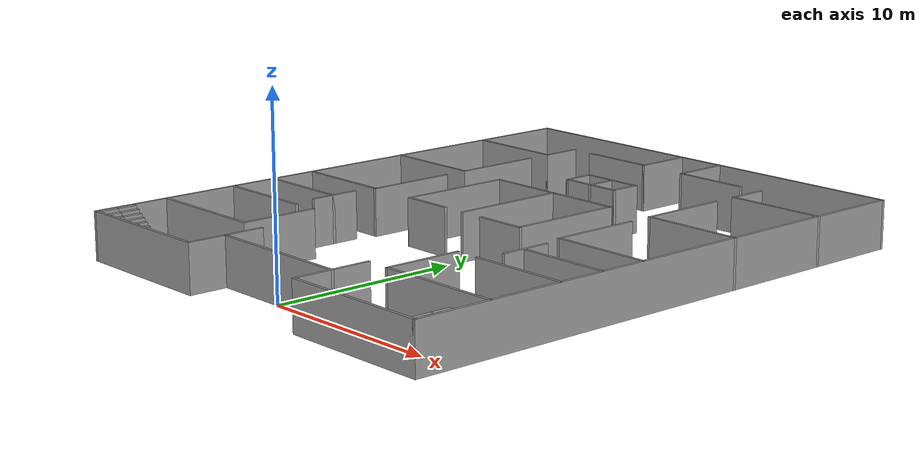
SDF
<?xml version='1.0'?>
<sdf version='1.6'>
  <model name='hospital_01'>
    <pose frame=''>0 13 0 0 -0 0</pose>
    <link name='Stairs_2'>
      <visual name='Stairs_2_Visual_0'>
        <pose frame=''>-8.53752 -14.4321 0.083333 0 -0 -1.5708</pose>
        <geometry>
          <box>
            <size>1 0.233333 0.166667</size>
          </box>
        </geometry>
        <material>
          <script>
            <uri>file://media/materials/scripts/gazebo.material</uri>
            <name>Gazebo/Grey</name>
          </script>
          <ambient>1 1 1 1</ambient>
        </material>
        <meta>
          <layer>0</layer>
        </meta>
      </visual>
      <collision name='Stairs_2_Collision_0'>
        <geometry>
          <box>
            <size>1 0.233333 0.166667</size>
          </box>
        </geometry>
        <pose frame=''>-8.53752 -14.4321 0.083333 0 -0 -1.5708</pose>
      </collision>
      <visual name='Stairs_2_Visual_1'>
        <pose frame=''>-8.77085 -14.4321 0.25 0 -0 -1.5708</pose>
        <geometry>
          <box>
            <size>1 0.233333 0.166667</size>
          </box>
        </geometry>
        <material>
          <script>
            <uri>file://media/materials/scripts/gazebo.material</uri>
            <name>Gazebo/Grey</name>
          </script>
          <ambient>1 1 1 1</ambient>
        </material>
        <meta>
          <layer>0</layer>
        </meta>
      </visual>
      <collision name='Stairs_2_Collision_1'>
        <geometry>
          <box>
            <size>1 0.233333 0.166667</size>
          </box>
        </geometry>
        <pose frame=''>-8.77085 -14.4321 0.25 0 -0 -1.5708</pose>
      </collision>
      <visual name='Stairs_2_Visual_2'>
        <pose frame=''>-9.00418 -14.4321 0.416667 0 -0 -1.5708</pose>
        <geometry>
          <box>
            <size>1 0.233333 0.166667</size>
          </box>
        </geometry>
        <material>
          <script>
            <uri>file://media/materials/scripts/gazebo.material</uri>
            <name>Gazebo/Grey</name>
          </script>
          <ambient>1 1 1 1</ambient>
        </material>
        <meta>
          <layer>0</layer>
        </meta>
      </visual>
      <collision name='Stairs_2_Collision_2'>
        <geometry>
          <box>
            <size>1 0.233333 0.166667</size>
          </box>
        </geometry>
        <pose frame=''>-9.00418 -14.4321 0.416667 0 -0 -1.5708</pose>
      </collision>
      <visual name='Stairs_2_Visual_3'>
        <pose frame=''>-9.23752 -14.4321 0.583333 0 -0 -1.5708</pose>
        <geometry>
          <box>
            <size>1 0.233333 0.166667</size>
          </box>
        </geometry>
        <material>
          <script>
            <uri>file://media/materials/scripts/gazebo.material</uri>
            <name>Gazebo/Grey</name>
          </script>
          <ambient>1 1 1 1</ambient>
        </material>
        <meta>
          <layer>0</layer>
        </meta>
      </visual>
      <collision name='Stairs_2_Collision_3'>
        <geometry>
          <box>
            <size>1 0.233333 0.166667</size>
          </box>
        </geometry>
        <pose frame=''>-9.23752 -14.4321 0.583333 0 -0 -1.5708</pose>
      </collision>
      <visual name='Stairs_2_Visual_4'>
        <pose frame=''>-9.47085 -14.4321 0.75 0 -0 -1.5708</pose>
        <geometry>
          <box>
            <size>1 0.233333 0.166667</size>
          </box>
        </geometry>
        <material>
          <script>
            <uri>file://media/materials/scripts/gazebo.material</uri>
            <name>Gazebo/Grey</name>
          </script>
          <ambient>1 1 1 1</ambient>
        </material>
        <meta>
          <layer>0</layer>
        </meta>
      </visual>
      <collision name='Stairs_2_Collision_4'>
        <geometry>
          <box>
            <size>1 0.233333 0.166667</size>
          </box>
        </geometry>
        <pose frame=''>-9.47085 -14.4321 0.75 0 -0 -1.5708</pose>
      </collision>
      <visual name='Stairs_2_Visual_5'>
        <pose frame=''>-9.70418 -14.4321 0.916667 0 -0 -1.5708</pose>
        <geometry>
          <box>
            <size>1 0.233333 0.166667</size>
          </box>
        </geometry>
        <material>
          <script>
            <uri>file://media/materials/scripts/gazebo.material</uri>
            <name>Gazebo/Grey</name>
          </script>
          <ambient>1 1 1 1</ambient>
        </material>
        <meta>
          <layer>0</layer>
        </meta>
      </visual>
      <collision name='Stairs_2_Collision_5'>
        <geometry>
          <box>
            <size>1 0.233333 0.166667</size>
          </box>
        </geometry>
        <pose frame=''>-9.70418 -14.4321 0.916667 0 -0 -1.5708</pose>
      </collision>
      <visual name='Stairs_2_Visual_6'>
        <pose frame=''>-9.93751 -14.432 1.08333 0 -0 -1.5708</pose>
        <geometry>
          <box>
            <size>1 0.233333 0.166667</size>
          </box>
        </geometry>
        <material>
          <script>
            <uri>file://media/materials/scripts/gazebo.material</uri>
            <name>Gazebo/Grey</name>
          </script>
          <ambient>1 1 1 1</ambient>
        </material>
        <meta>
          <layer>0</layer>
        </meta>
      </visual>
      <collision name='Stairs_2_Collision_6'>
        <geometry>
          <box>
            <size>1 0.233333 0.166667</size>
          </box>
        </geometry>
        <pose frame=''>-9.93751 -14.432 1.08333 0 -0 -1.5708</pose>
      </collision>
      <visual name='Stairs_2_Visual_7'>
        <pose frame=''>-10.1708 -14.432 1.25 0 -0 -1.5708</pose>
        <geometry>
          <box>
            <size>1 0.233333 0.166667</size>
          </box>
        </geometry>
        <material>
          <script>
            <uri>file://media/materials/scripts/gazebo.material</uri>
            <name>Gazebo/Grey</name>
          </script>
          <ambient>1 1 1 1</ambient>
        </material>
        <meta>
          <layer>0</layer>
        </meta>
      </visual>
      <collision name='Stairs_2_Collision_7'>
        <geometry>
          <box>
            <size>1 0.233333 0.166667</size>
          </box>
        </geometry>
        <pose frame=''>-10.1708 -14.432 1.25 0 -0 -1.5708</pose>
      </collision>
      <visual name='Stairs_2_Visual_8'>
        <pose frame=''>-10.4042 -14.432 1.41667 0 -0 -1.5708</pose>
        <geometry>
          <box>
            <size>1 0.233333 0.166667</size>
          </box>
        </geometry>
        <material>
          <script>
            <uri>file://media/materials/scripts/gazebo.material</uri>
            <name>Gazebo/Grey</name>
          </script>
          <ambient>1 1 1 1</ambient>
        </material>
        <meta>
          <layer>0</layer>
        </meta>
      </visual>
      <collision name='Stairs_2_Collision_8'>
        <geometry>
          <box>
            <size>1 0.233333 0.166667</size>
          </box>
        </geometry>
        <pose frame=''>-10.4042 -14.432 1.41667 0 -0 -1.5708</pose>
      </collision>
      <visual name='Stairs_2_Visual_9'>
        <pose frame=''>-10.6375 -14.432 1.58333 0 -0 -1.5708</pose>
        <geometry>
          <box>
            <size>1 0.233333 0.166667</size>
          </box>
        </geometry>
        <material>
          <script>
            <uri>file://media/materials/scripts/gazebo.material</uri>
            <name>Gazebo/Grey</name>
          </script>
          <ambient>1 1 1 1</ambient>
        </material>
        <meta>
          <layer>0</layer>
        </meta>
      </visual>
      <collision name='Stairs_2_Collision_9'>
        <geometry>
          <box>
            <size>1 0.233333 0.166667</size>
          </box>
        </geometry>
        <pose frame=''>-10.6375 -14.432 1.58333 0 -0 -1.5708</pose>
      </collision>
      <visual name='Stairs_2_Visual_10'>
        <pose frame=''>-10.8708 -14.432 1.75 0 -0 -1.5708</pose>
        <geometry>
          <box>
            <size>1 0.233333 0.166667</size>
          </box>
        </geometry>
        <material>
          <script>
            <uri>file://media/materials/scripts/gazebo.material</uri>
            <name>Gazebo/Grey</name>
          </script>
          <ambient>1 1 1 1</ambient>
        </material>
        <meta>
          <layer>0</layer>
        </meta>
      </visual>
      <collision name='Stairs_2_Collision_10'>
        <geometry>
          <box>
            <size>1 0.233333 0.166667</size>
          </box>
        </geometry>
        <pose frame=''>-10.8708 -14.432 1.75 0 -0 -1.5708</pose>
      </collision>
      <visual name='Stairs_2_Visual_11'>
        <pose frame=''>-11.1042 -14.432 1.91667 0 -0 -1.5708</pose>
        <geometry>
          <box>
            <size>1 0.233333 0.166667</size>
          </box>
        </geometry>
        <material>
          <script>
            <uri>file://media/materials/scripts/gazebo.material</uri>
            <name>Gazebo/Grey</name>
          </script>
          <ambient>1 1 1 1</ambient>
        </material>
        <meta>
          <layer>0</layer>
        </meta>
      </visual>
      <collision name='Stairs_2_Collision_11'>
        <geometry>
          <box>
            <size>1 0.233333 0.166667</size>
          </box>
        </geometry>
        <pose frame=''>-11.1042 -14.432 1.91667 0 -0 -1.5708</pose>
      </collision>
      <visual name='Stairs_2_Visual_12'>
        <pose frame=''>-11.3375 -14.432 2.08333 0 -0 -1.5708</pose>
        <geometry>
          <box>
            <size>1 0.233333 0.166667</size>
          </box>
        </geometry>
        <material>
          <script>
            <uri>file://media/materials/scripts/gazebo.material</uri>
            <name>Gazebo/Grey</name>
          </script>
          <ambient>1 1 1 1</ambient>
        </material>
        <meta>
          <layer>0</layer>
        </meta>
      </visual>
      <collision name='Stairs_2_Collision_12'>
        <geometry>
          <box>
            <size>1 0.233333 0.166667</size>
          </box>
        </geometry>
        <pose frame=''>-11.3375 -14.432 2.08333 0 -0 -1.5708</pose>
      </collision>
      <visual name='Stairs_2_Visual_13'>
        <pose frame=''>-11.5708 -14.432 2.25 0 -0 -1.5708</pose>
        <geometry>
          <box>
            <size>1 0.233333 0.166667</size>
          </box>
        </geometry>
        <material>
          <script>
            <uri>file://media/materials/scripts/gazebo.material</uri>
            <name>Gazebo/Grey</name>
          </script>
          <ambient>1 1 1 1</ambient>
        </material>
        <meta>
          <layer>0</layer>
        </meta>
      </visual>
      <collision name='Stairs_2_Collision_13'>
        <geometry>
          <box>
            <size>1 0.233333 0.166667</size>
          </box>
        </geometry>
        <pose frame=''>-11.5708 -14.432 2.25 0 -0 -1.5708</pose>
      </collision>
      <visual name='Stairs_2_Visual_14'>
        <pose frame=''>-11.8042 -14.432 2.41667 0 -0 -1.5708</pose>
        <geometry>
          <box>
            <size>1 0.233333 0.166667</size>
          </box>
        </geometry>
        <material>
          <script>
            <uri>file://media/materials/scripts/gazebo.material</uri>
            <name>Gazebo/Grey</name>
          </script>
          <ambient>1 1 1 1</ambient>
        </material>
        <meta>
          <layer>0</layer>
        </meta>
      </visual>
      <collision name='Stairs_2_Collision_14'>
        <geometry>
          <box>
            <size>1 0.233333 0.166667</size>
          </box>
        </geometry>
        <pose frame=''>-11.8042 -14.432 2.41667 0 -0 -1.5708</pose>
      </collision>
    </link>
    <link name='Stairs_6'>
      <visual name='Stairs_6_Visual_0'>
        <pose frame=''>-8.53689 -13.4368 0.083333 0 -0 -1.5708</pose>
        <geometry>
          <box>
            <size>1 0.233333 0.166667</size>
          </box>
        </geometry>
        <material>
          <script>
            <uri>file://media/materials/scripts/gazebo.material</uri>
            <name>Gazebo/Grey</name>
          </script>
          <ambient>1 1 1 1</ambient>
        </material>
        <meta>
          <layer>0</layer>
        </meta>
      </visual>
      <collision name='Stairs_6_Collision_0'>
        <geometry>
          <box>
            <size>1 0.233333 0.166667</size>
          </box>
        </geometry>
        <pose frame=''>-8.53689 -13.4368 0.083333 0 -0 -1.5708</pose>
      </collision>
      <visual name='Stairs_6_Visual_1'>
        <pose frame=''>-8.77022 -13.4368 0.25 0 -0 -1.5708</pose>
        <geometry>
          <box>
            <size>1 0.233333 0.166667</size>
          </box>
        </geometry>
        <material>
          <script>
            <uri>file://media/materials/scripts/gazebo.material</uri>
            <name>Gazebo/Grey</name>
          </script>
          <ambient>1 1 1 1</ambient>
        </material>
        <meta>
          <layer>0</layer>
        </meta>
      </visual>
      <collision name='Stairs_6_Collision_1'>
        <geometry>
          <box>
            <size>1 0.233333 0.166667</size>
          </box>
        </geometry>
        <pose frame=''>-8.77022 -13.4368 0.25 0 -0 -1.5708</pose>
      </collision>
      <visual name='Stairs_6_Visual_2'>
        <pose frame=''>-9.00356 -13.4368 0.416667 0 -0 -1.5708</pose>
        <geometry>
          <box>
            <size>1 0.233333 0.166667</size>
          </box>
        </geometry>
        <material>
          <script>
            <uri>file://media/materials/scripts/gazebo.material</uri>
            <name>Gazebo/Grey</name>
          </script>
          <ambient>1 1 1 1</ambient>
        </material>
        <meta>
          <layer>0</layer>
        </meta>
      </visual>
      <collision name='Stairs_6_Collision_2'>
        <geometry>
          <box>
            <size>1 0.233333 0.166667</size>
          </box>
        </geometry>
        <pose frame=''>-9.00356 -13.4368 0.416667 0 -0 -1.5708</pose>
      </collision>
      <visual name='Stairs_6_Visual_3'>
        <pose frame=''>-9.23689 -13.4368 0.583333 0 -0 -1.5708</pose>
        <geometry>
          <box>
            <size>1 0.233333 0.166667</size>
          </box>
        </geometry>
        <material>
          <script>
            <uri>file://media/materials/scripts/gazebo.material</uri>
            <name>Gazebo/Grey</name>
          </script>
          <ambient>1 1 1 1</ambient>
        </material>
        <meta>
          <layer>0</layer>
        </meta>
      </visual>
      <collision name='Stairs_6_Collision_3'>
        <geometry>
          <box>
            <size>1 0.233333 0.166667</size>
          </box>
        </geometry>
        <pose frame=''>-9.23689 -13.4368 0.583333 0 -0 -1.5708</pose>
      </collision>
      <visual name='Stairs_6_Visual_4'>
        <pose frame=''>-9.47022 -13.4368 0.75 0 -0 -1.5708</pose>
        <geometry>
          <box>
            <size>1 0.233333 0.166667</size>
          </box>
        </geometry>
        <material>
          <script>
            <uri>file://media/materials/scripts/gazebo.material</uri>
            <name>Gazebo/Grey</name>
          </script>
          <ambient>1 1 1 1</ambient>
        </material>
        <meta>
          <layer>0</layer>
        </meta>
      </visual>
      <collision name='Stairs_6_Collision_4'>
        <geometry>
          <box>
            <size>1 0.233333 0.166667</size>
          </box>
        </geometry>
        <pose frame=''>-9.47022 -13.4368 0.75 0 -0 -1.5708</pose>
      </collision>
      <visual name='Stairs_6_Visual_5'>
        <pose frame=''>-9.70356 -13.4368 0.916667 0 -0 -1.5708</pose>
        <geometry>
          <box>
            <size>1 0.233333 0.166667</size>
          </box>
        </geometry>
        <material>
          <script>
            <uri>file://media/materials/scripts/gazebo.material</uri>
            <name>Gazebo/Grey</name>
          </script>
          <ambient>1 1 1 1</ambient>
        </material>
        <meta>
          <layer>0</layer>
        </meta>
      </visual>
      <collision name='Stairs_6_Collision_5'>
        <geometry>
          <box>
            <size>1 0.233333 0.166667</size>
          </box>
        </geometry>
        <pose frame=''>-9.70356 -13.4368 0.916667 0 -0 -1.5708</pose>
      </collision>
      <visual name='Stairs_6_Visual_6'>
        <pose frame=''>-9.93689 -13.4368 1.08333 0 -0 -1.5708</pose>
        <geometry>
          <box>
            <size>1 0.233333 0.166667</size>
          </box>
        </geometry>
        <material>
          <script>
            <uri>file://media/materials/scripts/gazebo.material</uri>
            <name>Gazebo/Grey</name>
          </script>
          <ambient>1 1 1 1</ambient>
        </material>
        <meta>
          <layer>0</layer>
        </meta>
      </visual>
      <collision name='Stairs_6_Collision_6'>
        <geometry>
          <box>
            <size>1 0.233333 0.166667</size>
          </box>
        </geometry>
        <pose frame=''>-9.93689 -13.4368 1.08333 0 -0 -1.5708</pose>
      </collision>
      <visual name='Stairs_6_Visual_7'>
        <pose frame=''>-10.1702 -13.4368 1.25 0 -0 -1.5708</pose>
        <geometry>
          <box>
            <size>1 0.233333 0.166667</size>
          </box>
        </geometry>
        <material>
          <script>
            <uri>file://media/materials/scripts/gazebo.material</uri>
            <name>Gazebo/Grey</name>
          </script>
          <ambient>1 1 1 1</ambient>
        </material>
        <meta>
          <layer>0</layer>
        </meta>
      </visual>
      <collision name='Stairs_6_Collision_7'>
        <geometry>
          <box>
            <size>1 0.233333 0.166667</size>
          </box>
        </geometry>
        <pose frame=''>-10.1702 -13.4368 1.25 0 -0 -1.5708</pose>
      </collision>
      <visual name='Stairs_6_Visual_8'>
        <pose frame=''>-10.4036 -13.4368 1.41667 0 -0 -1.5708</pose>
        <geometry>
          <box>
            <size>1 0.233333 0.166667</size>
          </box>
        </geometry>
        <material>
          <script>
            <uri>file://media/materials/scripts/gazebo.material</uri>
            <name>Gazebo/Grey</name>
          </script>
          <ambient>1 1 1 1</ambient>
        </material>
        <meta>
          <layer>0</layer>
        </meta>
      </visual>
      <collision name='Stairs_6_Collision_8'>
        <geometry>
          <box>
            <size>1 0.233333 0.166667</size>
          </box>
        </geometry>
        <pose frame=''>-10.4036 -13.4368 1.41667 0 -0 -1.5708</pose>
      </collision>
      <visual name='Stairs_6_Visual_9'>
        <pose frame=''>-10.6369 -13.4368 1.58333 0 -0 -1.5708</pose>
        <geometry>
          <box>
            <size>1 0.233333 0.166667</size>
          </box>
        </geometry>
        <material>
          <script>
            <uri>file://media/materials/scripts/gazebo.material</uri>
            <name>Gazebo/Grey</name>
          </script>
          <ambient>1 1 1 1</ambient>
        </material>
        <meta>
          <layer>0</layer>
        </meta>
      </visual>
      <collision name='Stairs_6_Collision_9'>
        <geometry>
          <box>
            <size>1 0.233333 0.166667</size>
          </box>
        </geometry>
        <pose frame=''>-10.6369 -13.4368 1.58333 0 -0 -1.5708</pose>
      </collision>
      <visual name='Stairs_6_Visual_10'>
        <pose frame=''>-10.8702 -13.4368 1.75 0 -0 -1.5708</pose>
        <geometry>
          <box>
            <size>1 0.233333 0.166667</size>
          </box>
        </geometry>
        <material>
          <script>
            <uri>file://media/materials/scripts/gazebo.material</uri>
            <name>Gazebo/Grey</name>
          </script>
          <ambient>1 1 1 1</ambient>
        </material>
        <meta>
          <layer>0</layer>
        </meta>
      </visual>
      <collision name='Stairs_6_Collision_10'>
        <geometry>
          <box>
            <size>1 0.233333 0.166667</size>
          </box>
        </geometry>
        <pose frame=''>-10.8702 -13.4368 1.75 0 -0 -1.5708</pose>
      </collision>
      <visual name='Stairs_6_Visual_11'>
        <pose frame=''>-11.1036 -13.4368 1.91667 0 -0 -1.5708</pose>
        <geometry>
          <box>
            <size>1 0.233333 0.166667</size>
          </box>
        </geometry>
        <material>
          <script>
            <uri>file://media/materials/scripts/gazebo.material</uri>
            <name>Gazebo/Grey</name>
          </script>
          <ambient>1 1 1 1</ambient>
        </material>
        <meta>
          <layer>0</layer>
        </meta>
      </visual>
      <collision name='Stairs_6_Collision_11'>
        <geometry>
          <box>
            <size>1 0.233333 0.166667</size>
          </box>
        </geometry>
        <pose frame=''>-11.1036 -13.4368 1.91667 0 -0 -1.5708</pose>
      </collision>
      <visual name='Stairs_6_Visual_12'>
        <pose frame=''>-11.3369 -13.4368 2.08333 0 -0 -1.5708</pose>
        <geometry>
          <box>
            <size>1 0.233333 0.166667</size>
          </box>
        </geometry>
        <material>
          <script>
            <uri>file://media/materials/scripts/gazebo.material</uri>
            <name>Gazebo/Grey</name>
          </script>
          <ambient>1 1 1 1</ambient>
        </material>
        <meta>
          <layer>0</layer>
        </meta>
      </visual>
      <collision name='Stairs_6_Collision_12'>
        <geometry>
          <box>
            <size>1 0.233333 0.166667</size>
          </box>
        </geometry>
        <pose frame=''>-11.3369 -13.4368 2.08333 0 -0 -1.5708</pose>
      </collision>
      <visual name='Stairs_6_Visual_13'>
        <pose frame=''>-11.5702 -13.4368 2.25 0 -0 -1.5708</pose>
        <geometry>
          <box>
            <size>1 0.233333 0.166667</size>
          </box>
        </geometry>
        <material>
          <script>
            <uri>file://media/materials/scripts/gazebo.material</uri>
            <name>Gazebo/Grey</name>
          </script>
          <ambient>1 1 1 1</ambient>
        </material>
        <meta>
          <layer>0</layer>
        </meta>
      </visual>
      <collision name='Stairs_6_Collision_13'>
        <geometry>
          <box>
            <size>1 0.233333 0.166667</size>
          </box>
        </geometry>
        <pose frame=''>-11.5702 -13.4368 2.25 0 -0 -1.5708</pose>
      </collision>
      <visual name='Stairs_6_Visual_14'>
        <pose frame=''>-11.8036 -13.4368 2.41667 0 -0 -1.5708</pose>
        <geometry>
          <box>
            <size>1 0.233333 0.166667</size>
          </box>
        </geometry>
        <material>
          <script>
            <uri>file://media/materials/scripts/gazebo.material</uri>
            <name>Gazebo/Grey</name>
          </script>
          <ambient>1 1 1 1</ambient>
        </material>
        <meta>
          <layer>0</layer>
        </meta>
      </visual>
      <collision name='Stairs_6_Collision_14'>
        <geometry>
          <box>
            <size>1 0.233333 0.166667</size>
          </box>
        </geometry>
        <pose frame=''>-11.8036 -13.4368 2.41667 0 -0 -1.5708</pose>
      </collision>
    </link>
    <link name='Stairs_7'>
      <visual name='Stairs_7_Visual_0'>
        <pose frame=''>8.53246 -13.4386 0.083333 0 -0 1.5708</pose>
        <geometry>
          <box>
            <size>1 0.233333 0.166667</size>
          </box>
        </geometry>
        <material>
          <script>
            <uri>file://media/materials/scripts/gazebo.material</uri>
            <name>Gazebo/Grey</name>
          </script>
          <ambient>1 1 1 1</ambient>
        </material>
        <meta>
          <layer>0</layer>
        </meta>
      </visual>
      <collision name='Stairs_7_Collision_0'>
        <geometry>
          <box>
            <size>1 0.233333 0.166667</size>
          </box>
        </geometry>
        <pose frame=''>8.53246 -13.4386 0.083333 0 -0 1.5708</pose>
      </collision>
      <visual name='Stairs_7_Visual_1'>
        <pose frame=''>8.7658 -13.4386 0.25 0 -0 1.5708</pose>
        <geometry>
          <box>
            <size>1 0.233333 0.166667</size>
          </box>
        </geometry>
        <material>
          <script>
            <uri>file://media/materials/scripts/gazebo.material</uri>
            <name>Gazebo/Grey</name>
          </script>
          <ambient>1 1 1 1</ambient>
        </material>
        <meta>
          <layer>0</layer>
        </meta>
      </visual>
      <collision name='Stairs_7_Collision_1'>
        <geometry>
          <box>
            <size>1 0.233333 0.166667</size>
          </box>
        </geometry>
        <pose frame=''>8.7658 -13.4386 0.25 0 -0 1.5708</pose>
      </collision>
      <visual name='Stairs_7_Visual_2'>
        <pose frame=''>8.99913 -13.4386 0.416667 0 -0 1.5708</pose>
        <geometry>
          <box>
            <size>1 0.233333 0.166667</size>
          </box>
        </geometry>
        <material>
          <script>
            <uri>file://media/materials/scripts/gazebo.material</uri>
            <name>Gazebo/Grey</name>
          </script>
          <ambient>1 1 1 1</ambient>
        </material>
        <meta>
          <layer>0</layer>
        </meta>
      </visual>
      <collision name='Stairs_7_Collision_2'>
        <geometry>
          <box>
            <size>1 0.233333 0.166667</size>
          </box>
        </geometry>
        <pose frame=''>8.99913 -13.4386 0.416667 0 -0 1.5708</pose>
      </collision>
      <visual name='Stairs_7_Visual_3'>
        <pose frame=''>9.23246 -13.4386 0.583333 0 -0 1.5708</pose>
        <geometry>
          <box>
            <size>1 0.233333 0.166667</size>
          </box>
        </geometry>
        <material>
          <script>
            <uri>file://media/materials/scripts/gazebo.material</uri>
            <name>Gazebo/Grey</name>
          </script>
          <ambient>1 1 1 1</ambient>
        </material>
        <meta>
          <layer>0</layer>
        </meta>
      </visual>
      <collision name='Stairs_7_Collision_3'>
        <geometry>
          <box>
            <size>1 0.233333 0.166667</size>
          </box>
        </geometry>
        <pose frame=''>9.23246 -13.4386 0.583333 0 -0 1.5708</pose>
      </collision>
      <visual name='Stairs_7_Visual_4'>
        <pose frame=''>9.4658 -13.4386 0.75 0 -0 1.5708</pose>
        <geometry>
          <box>
            <size>1 0.233333 0.166667</size>
          </box>
        </geometry>
        <material>
          <script>
            <uri>file://media/materials/scripts/gazebo.material</uri>
            <name>Gazebo/Grey</name>
          </script>
          <ambient>1 1 1 1</ambient>
        </material>
        <meta>
          <layer>0</layer>
        </meta>
      </visual>
      <collision name='Stairs_7_Collision_4'>
        <geometry>
          <box>
            <size>1 0.233333 0.166667</size>
          </box>
        </geometry>
        <pose frame=''>9.4658 -13.4386 0.75 0 -0 1.5708</pose>
      </collision>
      <visual name='Stairs_7_Visual_5'>
        <pose frame=''>9.69913 -13.4386 0.916667 0 -0 1.5708</pose>
        <geometry>
          <box>
            <size>1 0.233333 0.166667</size>
          </box>
        </geometry>
        <material>
          <script>
            <uri>file://media/materials/scripts/gazebo.material</uri>
            <name>Gazebo/Grey</name>
          </script>
          <ambient>1 1 1 1</ambient>
        </material>
        <meta>
          <layer>0</layer>
        </meta>
      </visual>
      <collision name='Stairs_7_Collision_5'>
        <geometry>
          <box>
            <size>1 0.233333 0.166667</size>
          </box>
        </geometry>
        <pose frame=''>9.69913 -13.4386 0.916667 0 -0 1.5708</pose>
      </collision>
      <visual name='Stairs_7_Visual_6'>
        <pose frame=''>9.93246 -13.4386 1.08333 0 -0 1.5708</pose>
        <geometry>
          <box>
            <size>1 0.233333 0.166667</size>
          </box>
        </geometry>
        <material>
          <script>
            <uri>file://media/materials/scripts/gazebo.material</uri>
            <name>Gazebo/Grey</name>
          </script>
          <ambient>1 1 1 1</ambient>
        </material>
        <meta>
          <layer>0</layer>
        </meta>
      </visual>
      <collision name='Stairs_7_Collision_6'>
        <geometry>
          <box>
            <size>1 0.233333 0.166667</size>
          </box>
        </geometry>
        <pose frame=''>9.93246 -13.4386 1.08333 0 -0 1.5708</pose>
      </collision>
      <visual name='Stairs_7_Visual_7'>
        <pose frame=''>10.1658 -13.4386 1.25 0 -0 1.5708</pose>
        <geometry>
          <box>
            <size>1 0.233333 0.166667</size>
          </box>
        </geometry>
        <material>
          <script>
            <uri>file://media/materials/scripts/gazebo.material</uri>
            <name>Gazebo/Grey</name>
          </script>
          <ambient>1 1 1 1</ambient>
        </material>
        <meta>
          <layer>0</layer>
        </meta>
      </visual>
      <collision name='Stairs_7_Collision_7'>
        <geometry>
          <box>
            <size>1 0.233333 0.166667</size>
          </box>
        </geometry>
        <pose frame=''>10.1658 -13.4386 1.25 0 -0 1.5708</pose>
      </collision>
      <visual name='Stairs_7_Visual_8'>
        <pose frame=''>10.3991 -13.4386 1.41667 0 -0 1.5708</pose>
        <geometry>
          <box>
            <size>1 0.233333 0.166667</size>
          </box>
        </geometry>
        <material>
          <script>
            <uri>file://media/materials/scripts/gazebo.material</uri>
            <name>Gazebo/Grey</name>
          </script>
          <ambient>1 1 1 1</ambient>
        </material>
        <meta>
          <layer>0</layer>
        </meta>
      </visual>
      <collision name='Stairs_7_Collision_8'>
        <geometry>
          <box>
            <size>1 0.233333 0.166667</size>
          </box>
        </geometry>
        <pose frame=''>10.3991 -13.4386 1.41667 0 -0 1.5708</pose>
      </collision>
      <visual name='Stairs_7_Visual_9'>
        <pose frame=''>10.6325 -13.4386 1.58333 0 -0 1.5708</pose>
        <geometry>
          <box>
            <size>1 0.233333 0.166667</size>
          </box>
        </geometry>
        <material>
          <script>
            <uri>file://media/materials/scripts/gazebo.material</uri>
            <name>Gazebo/Grey</name>
          </script>
          <ambient>1 1 1 1</ambient>
        </material>
        <meta>
          <layer>0</layer>
        </meta>
      </visual>
      <collision name='Stairs_7_Collision_9'>
        <geometry>
          <box>
            <size>1 0.233333 0.166667</size>
          </box>
        </geometry>
        <pose frame=''>10.6325 -13.4386 1.58333 0 -0 1.5708</pose>
      </collision>
      <visual name='Stairs_7_Visual_10'>
        <pose frame=''>10.8658 -13.4386 1.75 0 -0 1.5708</pose>
        <geometry>
          <box>
            <size>1 0.233333 0.166667</size>
          </box>
        </geometry>
        <material>
          <script>
            <uri>file://media/materials/scripts/gazebo.material</uri>
            <name>Gazebo/Grey</name>
          </script>
          <ambient>1 1 1 1</ambient>
        </material>
        <meta>
          <layer>0</layer>
        </meta>
      </visual>
      <collision name='Stairs_7_Collision_10'>
        <geometry>
          <box>
            <size>1 0.233333 0.166667</size>
          </box>
        </geometry>
        <pose frame=''>10.8658 -13.4386 1.75 0 -0 1.5708</pose>
      </collision>
      <visual name='Stairs_7_Visual_11'>
        <pose frame=''>11.0991 -13.4386 1.91667 0 -0 1.5708</pose>
        <geometry>
          <box>
            <size>1 0.233333 0.166667</size>
          </box>
        </geometry>
        <material>
          <script>
            <uri>file://media/materials/scripts/gazebo.material</uri>
            <name>Gazebo/Grey</name>
          </script>
          <ambient>1 1 1 1</ambient>
        </material>
        <meta>
          <layer>0</layer>
        </meta>
      </visual>
      <collision name='Stairs_7_Collision_11'>
        <geometry>
          <box>
            <size>1 0.233333 0.166667</size>
          </box>
        </geometry>
        <pose frame=''>11.0991 -13.4386 1.91667 0 -0 1.5708</pose>
      </collision>
      <visual name='Stairs_7_Visual_12'>
        <pose frame=''>11.3325 -13.4386 2.08333 0 -0 1.5708</pose>
        <geometry>
          <box>
            <size>1 0.233333 0.166667</size>
          </box>
        </geometry>
        <material>
          <script>
            <uri>file://media/materials/scripts/gazebo.material</uri>
            <name>Gazebo/Grey</name>
          </script>
          <ambient>1 1 1 1</ambient>
        </material>
        <meta>
          <layer>0</layer>
        </meta>
      </visual>
      <collision name='Stairs_7_Collision_12'>
        <geometry>
          <box>
            <size>1 0.233333 0.166667</size>
          </box>
        </geometry>
        <pose frame=''>11.3325 -13.4386 2.08333 0 -0 1.5708</pose>
      </collision>
      <visual name='Stairs_7_Visual_13'>
        <pose frame=''>11.5658 -13.4386 2.25 0 -0 1.5708</pose>
        <geometry>
          <box>
            <size>1 0.233333 0.166667</size>
          </box>
        </geometry>
        <material>
          <script>
            <uri>file://media/materials/scripts/gazebo.material</uri>
            <name>Gazebo/Grey</name>
          </script>
          <ambient>1 1 1 1</ambient>
        </material>
        <meta>
          <layer>0</layer>
        </meta>
      </visual>
      <collision name='Stairs_7_Collision_13'>
        <geometry>
          <box>
            <size>1 0.233333 0.166667</size>
          </box>
        </geometry>
        <pose frame=''>11.5658 -13.4386 2.25 0 -0 1.5708</pose>
      </collision>
      <visual name='Stairs_7_Visual_14'>
        <pose frame=''>11.7991 -13.4386 2.41667 0 -0 1.5708</pose>
        <geometry>
          <box>
            <size>1 0.233333 0.166667</size>
          </box>
        </geometry>
        <material>
          <script>
            <uri>file://media/materials/scripts/gazebo.material</uri>
            <name>Gazebo/Grey</name>
          </script>
          <ambient>1 1 1 1</ambient>
        </material>
        <meta>
          <layer>0</layer>
        </meta>
      </visual>
      <collision name='Stairs_7_Collision_14'>
        <geometry>
          <box>
            <size>1 0.233333 0.166667</size>
          </box>
        </geometry>
        <pose frame=''>11.7991 -13.4386 2.41667 0 -0 1.5708</pose>
      </collision>
    </link>
    <link name='Stairs_8'>
      <visual name='Stairs_8_Visual_0'>
        <pose frame=''>8.53246 -14.4268 0.083333 0 -0 1.5708</pose>
        <geometry>
          <box>
            <size>1 0.233333 0.166667</size>
          </box>
        </geometry>
        <material>
          <script>
            <uri>file://media/materials/scripts/gazebo.material</uri>
            <name>Gazebo/Grey</name>
          </script>
          <ambient>1 1 1 1</ambient>
        </material>
        <meta>
          <layer>0</layer>
        </meta>
      </visual>
      <collision name='Stairs_8_Collision_0'>
        <geometry>
          <box>
            <size>1 0.233333 0.166667</size>
          </box>
        </geometry>
        <pose frame=''>8.53246 -14.4268 0.083333 0 -0 1.5708</pose>
      </collision>
      <visual name='Stairs_8_Visual_1'>
        <pose frame=''>8.7658 -14.4268 0.25 0 -0 1.5708</pose>
        <geometry>
          <box>
            <size>1 0.233333 0.166667</size>
          </box>
        </geometry>
        <material>
          <script>
            <uri>file://media/materials/scripts/gazebo.material</uri>
            <name>Gazebo/Grey</name>
          </script>
          <ambient>1 1 1 1</ambient>
        </material>
        <meta>
          <layer>0</layer>
        </meta>
      </visual>
      <collision name='Stairs_8_Collision_1'>
        <geometry>
          <box>
            <size>1 0.233333 0.166667</size>
          </box>
        </geometry>
        <pose frame=''>8.7658 -14.4268 0.25 0 -0 1.5708</pose>
      </collision>
      <visual name='Stairs_8_Visual_2'>
        <pose frame=''>8.99913 -14.4268 0.416667 0 -0 1.5708</pose>
        <geometry>
          <box>
            <size>1 0.233333 0.166667</size>
          </box>
        </geometry>
        <material>
          <script>
            <uri>file://media/materials/scripts/gazebo.material</uri>
            <name>Gazebo/Grey</name>
          </script>
          <ambient>1 1 1 1</ambient>
        </material>
        <meta>
          <layer>0</layer>
        </meta>
      </visual>
      <collision name='Stairs_8_Collision_2'>
        <geometry>
          <box>
            <size>1 0.233333 0.166667</size>
          </box>
        </geometry>
        <pose frame=''>8.99913 -14.4268 0.416667 0 -0 1.5708</pose>
      </collision>
      <visual name='Stairs_8_Visual_3'>
        <pose frame=''>9.23246 -14.4268 0.583333 0 -0 1.5708</pose>
        <geometry>
          <box>
            <size>1 0.233333 0.166667</size>
          </box>
        </geometry>
        <material>
          <script>
            <uri>file://media/materials/scripts/gazebo.material</uri>
            <name>Gazebo/Grey</name>
          </script>
          <ambient>1 1 1 1</ambient>
        </material>
        <meta>
          <layer>0</layer>
        </meta>
      </visual>
      <collision name='Stairs_8_Collision_3'>
        <geometry>
          <box>
            <size>1 0.233333 0.166667</size>
          </box>
        </geometry>
        <pose frame=''>9.23246 -14.4268 0.583333 0 -0 1.5708</pose>
      </collision>
      <visual name='Stairs_8_Visual_4'>
        <pose frame=''>9.4658 -14.4268 0.75 0 -0 1.5708</pose>
        <geometry>
          <box>
            <size>1 0.233333 0.166667</size>
          </box>
        </geometry>
        <material>
          <script>
            <uri>file://media/materials/scripts/gazebo.material</uri>
            <name>Gazebo/Grey</name>
          </script>
          <ambient>1 1 1 1</ambient>
        </material>
        <meta>
          <layer>0</layer>
        </meta>
      </visual>
      <collision name='Stairs_8_Collision_4'>
        <geometry>
          <box>
            <size>1 0.233333 0.166667</size>
          </box>
        </geometry>
        <pose frame=''>9.4658 -14.4268 0.75 0 -0 1.5708</pose>
      </collision>
      <visual name='Stairs_8_Visual_5'>
        <pose frame=''>9.69913 -14.4268 0.916667 0 -0 1.5708</pose>
        <geometry>
          <box>
            <size>1 0.233333 0.166667</size>
          </box>
        </geometry>
        <material>
          <script>
            <uri>file://media/materials/scripts/gazebo.material</uri>
            <name>Gazebo/Grey</name>
          </script>
          <ambient>1 1 1 1</ambient>
        </material>
        <meta>
          <layer>0</layer>
        </meta>
      </visual>
      <collision name='Stairs_8_Collision_5'>
        <geometry>
          <box>
            <size>1 0.233333 0.166667</size>
          </box>
        </geometry>
        <pose frame=''>9.69913 -14.4268 0.916667 0 -0 1.5708</pose>
      </collision>
      <visual name='Stairs_8_Visual_6'>
        <pose frame=''>9.93246 -14.4268 1.08333 0 -0 1.5708</pose>
        <geometry>
          <box>
            <size>1 0.233333 0.166667</size>
          </box>
        </geometry>
        <material>
          <script>
            <uri>file://media/materials/scripts/gazebo.material</uri>
            <name>Gazebo/Grey</name>
          </script>
          <ambient>1 1 1 1</ambient>
        </material>
        <meta>
          <layer>0</layer>
        </meta>
      </visual>
      <collision name='Stairs_8_Collision_6'>
        <geometry>
          <box>
            <size>1 0.233333 0.166667</size>
          </box>
        </geometry>
        <pose frame=''>9.93246 -14.4268 1.08333 0 -0 1.5708</pose>
      </collision>
      <visual name='Stairs_8_Visual_7'>
        <pose frame=''>10.1658 -14.4268 1.25 0 -0 1.5708</pose>
        <geometry>
          <box>
            <size>1 0.233333 0.166667</size>
          </box>
        </geometry>
        <material>
          <script>
            <uri>file://media/materials/scripts/gazebo.material</uri>
            <name>Gazebo/Grey</name>
          </script>
          <ambient>1 1 1 1</ambient>
        </material>
        <meta>
          <layer>0</layer>
        </meta>
      </visual>
      <collision name='Stairs_8_Collision_7'>
        <geometry>
          <box>
            <size>1 0.233333 0.166667</size>
          </box>
        </geometry>
        <pose frame=''>10.1658 -14.4268 1.25 0 -0 1.5708</pose>
      </collision>
      <visual name='Stairs_8_Visual_8'>
        <pose frame=''>10.3991 -14.4268 1.41667 0 -0 1.5708</pose>
        <geometry>
          <box>
            <size>1 0.233333 0.166667</size>
          </box>
        </geometry>
        <material>
          <script>
            <uri>file://media/materials/scripts/gazebo.material</uri>
            <name>Gazebo/Grey</name>
          </script>
          <ambient>1 1 1 1</ambient>
        </material>
        <meta>
          <layer>0</layer>
        </meta>
      </visual>
      <collision name='Stairs_8_Collision_8'>
        <geometry>
          <box>
            <size>1 0.233333 0.166667</size>
          </box>
        </geometry>
        <pose frame=''>10.3991 -14.4268 1.41667 0 -0 1.5708</pose>
      </collision>
      <visual name='Stairs_8_Visual_9'>
        <pose frame=''>10.6325 -14.4268 1.58333 0 -0 1.5708</pose>
        <geometry>
          <box>
            <size>1 0.233333 0.166667</size>
          </box>
        </geometry>
        <material>
          <script>
            <uri>file://media/materials/scripts/gazebo.material</uri>
            <name>Gazebo/Grey</name>
          </script>
          <ambient>1 1 1 1</ambient>
        </material>
        <meta>
          <layer>0</layer>
        </meta>
      </visual>
      <collision name='Stairs_8_Collision_9'>
        <geometry>
          <box>
            <size>1 0.233333 0.166667</size>
          </box>
        </geometry>
        <pose frame=''>10.6325 -14.4268 1.58333 0 -0 1.5708</pose>
      </collision>
      <visual name='Stairs_8_Visual_10'>
        <pose frame=''>10.8658 -14.4268 1.75 0 -0 1.5708</pose>
        <geometry>
          <box>
            <size>1 0.233333 0.166667</size>
          </box>
        </geometry>
        <material>
          <script>
            <uri>file://media/materials/scripts/gazebo.material</uri>
            <name>Gazebo/Grey</name>
          </script>
          <ambient>1 1 1 1</ambient>
        </material>
        <meta>
          <layer>0</layer>
        </meta>
      </visual>
      <collision name='Stairs_8_Collision_10'>
        <geometry>
          <box>
            <size>1 0.233333 0.166667</size>
          </box>
        </geometry>
        <pose frame=''>10.8658 -14.4268 1.75 0 -0 1.5708</pose>
      </collision>
      <visual name='Stairs_8_Visual_11'>
        <pose frame=''>11.0991 -14.4268 1.91667 0 -0 1.5708</pose>
        <geometry>
          <box>
            <size>1 0.233333 0.166667</size>
          </box>
        </geometry>
        <material>
          <script>
            <uri>file://media/materials/scripts/gazebo.material</uri>
            <name>Gazebo/Grey</name>
          </script>
          <ambient>1 1 1 1</ambient>
        </material>
        <meta>
          <layer>0</layer>
        </meta>
      </visual>
      <collision name='Stairs_8_Collision_11'>
        <geometry>
          <box>
            <size>1 0.233333 0.166667</size>
          </box>
        </geometry>
        <pose frame=''>11.0991 -14.4268 1.91667 0 -0 1.5708</pose>
      </collision>
      <visual name='Stairs_8_Visual_12'>
        <pose frame=''>11.3325 -14.4268 2.08333 0 -0 1.5708</pose>
        <geometry>
          <box>
            <size>1 0.233333 0.166667</size>
          </box>
        </geometry>
        <material>
          <script>
            <uri>file://media/materials/scripts/gazebo.material</uri>
            <name>Gazebo/Grey</name>
          </script>
          <ambient>1 1 1 1</ambient>
        </material>
        <meta>
          <layer>0</layer>
        </meta>
      </visual>
      <collision name='Stairs_8_Collision_12'>
        <geometry>
          <box>
            <size>1 0.233333 0.166667</size>
          </box>
        </geometry>
        <pose frame=''>11.3325 -14.4268 2.08333 0 -0 1.5708</pose>
      </collision>
      <visual name='Stairs_8_Visual_13'>
        <pose frame=''>11.5658 -14.4268 2.25 0 -0 1.5708</pose>
        <geometry>
          <box>
            <size>1 0.233333 0.166667</size>
          </box>
        </geometry>
        <material>
          <script>
            <uri>file://media/materials/scripts/gazebo.material</uri>
            <name>Gazebo/Grey</name>
          </script>
          <ambient>1 1 1 1</ambient>
        </material>
        <meta>
          <layer>0</layer>
        </meta>
      </visual>
      <collision name='Stairs_8_Collision_13'>
        <geometry>
          <box>
            <size>1 0.233333 0.166667</size>
          </box>
        </geometry>
        <pose frame=''>11.5658 -14.4268 2.25 0 -0 1.5708</pose>
      </collision>
      <visual name='Stairs_8_Visual_14'>
        <pose frame=''>11.7991 -14.4268 2.41667 0 -0 1.5708</pose>
        <geometry>
          <box>
            <size>1 0.233333 0.166667</size>
          </box>
        </geometry>
        <material>
          <script>
            <uri>file://media/materials/scripts/gazebo.material</uri>
            <name>Gazebo/Grey</name>
          </script>
          <ambient>1 1 1 1</ambient>
        </material>
        <meta>
          <layer>0</layer>
        </meta>
      </visual>
      <collision name='Stairs_8_Collision_14'>
        <geometry>
          <box>
            <size>1 0.233333 0.166667</size>
          </box>
        </geometry>
        <pose frame=''>11.7991 -14.4268 2.41667 0 -0 1.5708</pose>
      </collision>
    </link>
    <link name='Wall_107'>
      <collision name='Wall_107_Collision'>
        <geometry>
          <box>
            <size>6.15 0.15 2.5</size>
          </box>
        </geometry>
        <pose frame=''>0 0 1.25 0 -0 0</pose>
      </collision>
      <visual name='Wall_107_Visual'>
        <pose frame=''>0 0 1.25 0 -0 0</pose>
        <geometry>
          <box>
            <size>6.15 0.15 2.5</size>
          </box>
        </geometry>
        <material>
          <script>
            <uri>file://media/materials/scripts/gazebo.material</uri>
            <name>Gazebo/Grey</name>
          </script>
          <ambient>1 1 1 1</ambient>
        </material>
        <meta>
          <layer>0</layer>
        </meta>
      </visual>
      <pose frame=''>-4 1 0 0 -0 -1.5708</pose>
    </link>
    <link name='Wall_109'>
      <collision name='Wall_109_Collision'>
        <geometry>
          <box>
            <size>2.8 0.15 2.5</size>
          </box>
        </geometry>
        <pose frame=''>0 0 1.25 0 -0 0</pose>
      </collision>
      <visual name='Wall_109_Visual'>
        <pose frame=''>0 0 1.25 0 -0 0</pose>
        <geometry>
          <box>
            <size>2.8 0.15 2.5</size>
          </box>
        </geometry>
        <material>
          <script>
            <uri>file://media/materials/scripts/gazebo.material</uri>
            <name>Gazebo/Grey</name>
          </script>
          <ambient>1 1 1 1</ambient>
        </material>
        <meta>
          <layer>0</layer>
        </meta>
      </visual>
      <pose frame=''>-2.675 -2 0 0 -0 0</pose>
    </link>
    <link name='Wall_111'>
      <collision name='Wall_111_Collision'>
        <geometry>
          <box>
            <size>6.15 0.15 2.5</size>
          </box>
        </geometry>
        <pose frame=''>0 0 1.25 0 -0 0</pose>
      </collision>
      <visual name='Wall_111_Visual'>
        <pose frame=''>0 0 1.25 0 -0 0</pose>
        <geometry>
          <box>
            <size>6.15 0.15 2.5</size>
          </box>
        </geometry>
        <material>
          <script>
            <uri>file://media/materials/scripts/gazebo.material</uri>
            <name>Gazebo/Grey</name>
          </script>
          <ambient>1 1 1 1</ambient>
        </material>
        <meta>
          <layer>0</layer>
        </meta>
      </visual>
      <pose frame=''>4 1 0 0 -0 -1.5708</pose>
    </link>
    <link name='Wall_113'>
      <collision name='Wall_113_Collision'>
        <geometry>
          <box>
            <size>2.8 0.15 2.5</size>
          </box>
        </geometry>
        <pose frame=''>0 0 1.25 0 -0 0</pose>
      </collision>
      <visual name='Wall_113_Visual'>
        <pose frame=''>0 0 1.25 0 -0 0</pose>
        <geometry>
          <box>
            <size>2.8 0.15 2.5</size>
          </box>
        </geometry>
        <material>
          <script>
            <uri>file://media/materials/scripts/gazebo.material</uri>
            <name>Gazebo/Grey</name>
          </script>
          <ambient>1 1 1 1</ambient>
        </material>
        <meta>
          <layer>0</layer>
        </meta>
      </visual>
      <pose frame=''>2.675 -2 0 0 -0 3.14159</pose>
    </link>
    <link name='Wall_117'>
      <collision name='Wall_117_Collision'>
        <geometry>
          <box>
            <size>3.45 0.15 2.5</size>
          </box>
        </geometry>
        <pose frame=''>0 0 1.25 0 -0 0</pose>
      </collision>
      <visual name='Wall_117_Visual'>
        <pose frame=''>0 0 1.25 0 -0 0</pose>
        <geometry>
          <box>
            <size>3.45 0.15 2.5</size>
          </box>
        </geometry>
        <material>
          <script>
            <uri>file://media/materials/scripts/gazebo.material</uri>
            <name>Gazebo/Grey</name>
          </script>
          <ambient>1 1 1 1</ambient>
        </material>
        <meta>
          <layer>0</layer>
        </meta>
      </visual>
      <pose frame=''>0 8.2 0 0 -0 0</pose>
    </link>
    <link name='Wall_119'>
      <collision name='Wall_119_Collision'>
        <geometry>
          <box>
            <size>3.45 0.15 2.5</size>
          </box>
        </geometry>
        <pose frame=''>0 0 1.25 0 -0 0</pose>
      </collision>
      <visual name='Wall_119_Visual'>
        <pose frame=''>0 0 1.25 0 -0 0</pose>
        <geometry>
          <box>
            <size>3.45 0.15 2.5</size>
          </box>
        </geometry>
        <material>
          <script>
            <uri>file://media/materials/scripts/gazebo.material</uri>
            <name>Gazebo/Grey</name>
          </script>
          <ambient>1 1 1 1</ambient>
        </material>
        <meta>
          <layer>0</layer>
        </meta>
      </visual>
      <pose frame=''>0 6.65 0 0 -0 0</pose>
    </link>
    <link name='Wall_121'>
      <collision name='Wall_121_Collision'>
        <geometry>
          <box>
            <size>1.7 0.15 2.5</size>
          </box>
        </geometry>
        <pose frame=''>0 0 1.25 0 -0 0</pose>
      </collision>
      <visual name='Wall_121_Visual'>
        <pose frame=''>0 0 1.25 0 -0 0</pose>
        <geometry>
          <box>
            <size>1.7 0.15 2.5</size>
          </box>
        </geometry>
        <material>
          <script>
            <uri>file://media/materials/scripts/gazebo.material</uri>
            <name>Gazebo/Grey</name>
          </script>
          <ambient>1 1 1 1</ambient>
        </material>
        <meta>
          <layer>0</layer>
        </meta>
      </visual>
      <pose frame=''>0 7.425 0 0 -0 -1.5708</pose>
    </link>
    <link name='Wall_123'>
      <collision name='Wall_123_Collision'>
        <geometry>
          <box>
            <size>1.7 0.15 2.5</size>
          </box>
        </geometry>
        <pose frame=''>0 0 1.25 0 -0 0</pose>
      </collision>
      <visual name='Wall_123_Visual'>
        <pose frame=''>0 0 1.25 0 -0 0</pose>
        <geometry>
          <box>
            <size>1.7 0.15 2.5</size>
          </box>
        </geometry>
        <material>
          <script>
            <uri>file://media/materials/scripts/gazebo.material</uri>
            <name>Gazebo/Grey</name>
          </script>
          <ambient>1 1 1 1</ambient>
        </material>
        <meta>
          <layer>0</layer>
        </meta>
      </visual>
      <pose frame=''>-1.65 7.425 0 0 -0 -1.5708</pose>
    </link>
    <link name='Wall_125'>
      <collision name='Wall_125_Collision'>
        <geometry>
          <box>
            <size>1.7 0.15 2.5</size>
          </box>
        </geometry>
        <pose frame=''>0 0 1.25 0 -0 0</pose>
      </collision>
      <visual name='Wall_125_Visual'>
        <pose frame=''>0 0 1.25 0 -0 0</pose>
        <geometry>
          <box>
            <size>1.7 0.15 2.5</size>
          </box>
        </geometry>
        <material>
          <script>
            <uri>file://media/materials/scripts/gazebo.material</uri>
            <name>Gazebo/Grey</name>
          </script>
          <ambient>1 1 1 1</ambient>
        </material>
        <meta>
          <layer>0</layer>
        </meta>
      </visual>
      <pose frame=''>1.65 7.425 0 0 -0 -1.5708</pose>
    </link>
    <link name='Wall_129'>
      <collision name='Wall_129_Collision'>
        <geometry>
          <box>
            <size>24.15 0.15 2.5</size>
          </box>
        </geometry>
        <pose frame=''>0 0 1.25 0 -0 0</pose>
      </collision>
      <visual name='Wall_129_Visual'>
        <pose frame=''>0 0 1.25 0 -0 0</pose>
        <geometry>
          <box>
            <size>24.15 0.15 2.5</size>
          </box>
        </geometry>
        <material>
          <script>
            <uri>file://media/materials/scripts/gazebo.material</uri>
            <name>Gazebo/Grey</name>
          </script>
          <ambient>1 1 1 1</ambient>
        </material>
        <meta>
          <layer>0</layer>
        </meta>
      </visual>
      <pose frame=''>0 15 0 0 -0 3.14159</pose>
    </link>
    <link name='Wall_19'>
      <collision name='Wall_19_Collision'>
        <geometry>
          <box>
            <size>8.15 0.15 2.5</size>
          </box>
        </geometry>
        <pose frame=''>0 0 1.25 0 -0 0</pose>
      </collision>
      <visual name='Wall_19_Visual'>
        <pose frame=''>0 0 1.25 0 -0 0</pose>
        <geometry>
          <box>
            <size>8.15 0.15 2.5</size>
          </box>
        </geometry>
        <material>
          <script>
            <uri>file://media/materials/scripts/gazebo.material</uri>
            <name>Gazebo/Grey</name>
          </script>
          <ambient>1 1 1 1</ambient>
        </material>
        <meta>
          <layer>0</layer>
        </meta>
      </visual>
      <pose frame=''>0 -13 0 0 -0 0</pose>
    </link>
    <link name='Wall_21'>
      <collision name='Wall_21_Collision'>
        <geometry>
          <box>
            <size>4.15 0.15 2.5</size>
          </box>
        </geometry>
        <pose frame=''>0 0 1.25 0 -0 0</pose>
      </collision>
      <visual name='Wall_21_Visual'>
        <pose frame=''>0 0 1.25 0 -0 0</pose>
        <geometry>
          <box>
            <size>4.15 0.15 2.5</size>
          </box>
        </geometry>
        <material>
          <script>
            <uri>file://media/materials/scripts/gazebo.material</uri>
            <name>Gazebo/Grey</name>
          </script>
          <ambient>1 1 1 1</ambient>
        </material>
        <meta>
          <layer>0</layer>
        </meta>
      </visual>
      <pose frame=''>-4 -13 0 0 -0 1.5708</pose>
    </link>
    <link name='Wall_23'>
      <collision name='Wall_23_Collision'>
        <geometry>
          <box>
            <size>8.15 0.15 2.5</size>
          </box>
        </geometry>
        <pose frame=''>0 0 1.25 0 -0 0</pose>
      </collision>
      <visual name='Wall_23_Visual'>
        <pose frame=''>0 0 1.25 0 -0 0</pose>
        <geometry>
          <box>
            <size>8.15 0.15 2.5</size>
          </box>
        </geometry>
        <material>
          <script>
            <uri>file://media/materials/scripts/gazebo.material</uri>
            <name>Gazebo/Grey</name>
          </script>
          <ambient>1 1 1 1</ambient>
        </material>
        <meta>
          <layer>0</layer>
        </meta>
      </visual>
      <pose frame=''>-8 -15 0 0 -0 3.14159</pose>
    </link>
    <link name='Wall_26'>
      <collision name='Wall_26_Collision'>
        <geometry>
          <box>
            <size>6.8 0.15 2.5</size>
          </box>
        </geometry>
        <pose frame=''>0 0 1.25 0 -0 0</pose>
      </collision>
      <visual name='Wall_26_Visual'>
        <pose frame=''>0 0 1.25 0 -0 0</pose>
        <geometry>
          <box>
            <size>6.8 0.15 2.5</size>
          </box>
        </geometry>
        <material>
          <script>
            <uri>file://media/materials/scripts/gazebo.material</uri>
            <name>Gazebo/Grey</name>
          </script>
          <ambient>1 1 1 1</ambient>
        </material>
        <meta>
          <layer>0</layer>
        </meta>
      </visual>
      <pose frame=''>-8.675 -11 0 0 -0 0</pose>
    </link>
    <link name='Wall_30'>
      <collision name='Wall_30_Collision'>
        <geometry>
          <box>
            <size>4.15 0.15 2.5</size>
          </box>
        </geometry>
        <pose frame=''>0 0 1.25 0 -0 0</pose>
      </collision>
      <visual name='Wall_30_Visual'>
        <pose frame=''>0 0 1.25 0 -0 0</pose>
        <geometry>
          <box>
            <size>4.15 0.15 2.5</size>
          </box>
        </geometry>
        <material>
          <script>
            <uri>file://media/materials/scripts/gazebo.material</uri>
            <name>Gazebo/Grey</name>
          </script>
          <ambient>1 1 1 1</ambient>
        </material>
        <meta>
          <layer>0</layer>
        </meta>
      </visual>
      <pose frame=''>-5.35 -9 0 0 -0 1.5708</pose>
    </link>
    <link name='Wall_32'>
      <collision name='Wall_32_Collision'>
        <geometry>
          <box>
            <size>5.45 0.15 2.5</size>
          </box>
        </geometry>
        <pose frame=''>0 0 1.25 0 -0 0</pose>
      </collision>
      <visual name='Wall_32_Visual'>
        <pose frame=''>0 0 1.25 0 -0 0</pose>
        <geometry>
          <box>
            <size>5.45 0.15 2.5</size>
          </box>
        </geometry>
        <material>
          <script>
            <uri>file://media/materials/scripts/gazebo.material</uri>
            <name>Gazebo/Grey</name>
          </script>
          <ambient>1 1 1 1</ambient>
        </material>
        <meta>
          <layer>0</layer>
        </meta>
      </visual>
      <pose frame=''>-9.35 -7 0 0 -0 0</pose>
    </link>
    <link name='Wall_37'>
      <collision name='Wall_37_Collision'>
        <geometry>
          <box>
            <size>5.15 0.15 2.5</size>
          </box>
        </geometry>
        <pose frame=''>0 0 1.25 0 -0 0</pose>
      </collision>
      <visual name='Wall_37_Visual'>
        <pose frame=''>0 0 1.25 0 -0 0</pose>
        <geometry>
          <box>
            <size>5.15 0.15 2.5</size>
          </box>
        </geometry>
        <material>
          <script>
            <uri>file://media/materials/scripts/gazebo.material</uri>
            <name>Gazebo/Grey</name>
          </script>
          <ambient>1 1 1 1</ambient>
        </material>
        <meta>
          <layer>0</layer>
        </meta>
      </visual>
      <pose frame=''>-9.5 -4.5 0 0 -0 0</pose>
    </link>
    <link name='Wall_39'>
      <collision name='Wall_39_Collision'>
        <geometry>
          <box>
            <size>2.65 0.15 2.5</size>
          </box>
        </geometry>
        <pose frame=''>0 0 1.25 0 -0 0</pose>
      </collision>
      <visual name='Wall_39_Visual'>
        <pose frame=''>0 0 1.25 0 -0 0</pose>
        <geometry>
          <box>
            <size>2.65 0.15 2.5</size>
          </box>
        </geometry>
        <material>
          <script>
            <uri>file://media/materials/scripts/gazebo.material</uri>
            <name>Gazebo/Grey</name>
          </script>
          <ambient>1 1 1 1</ambient>
        </material>
        <meta>
          <layer>0</layer>
        </meta>
      </visual>
      <pose frame=''>-7 -4.4 0 0 -0 1.5708</pose>
    </link>
    <link name='Wall_43'>
      <collision name='Wall_43_Collision'>
        <geometry>
          <box>
            <size>5.45 0.15 2.5</size>
          </box>
        </geometry>
        <pose frame=''>0 0 1.25 0 -0 0</pose>
      </collision>
      <visual name='Wall_43_Visual'>
        <pose frame=''>0 0 1.25 0 -0 0</pose>
        <geometry>
          <box>
            <size>5.45 0.15 2.5</size>
          </box>
        </geometry>
        <material>
          <script>
            <uri>file://media/materials/scripts/gazebo.material</uri>
            <name>Gazebo/Grey</name>
          </script>
          <ambient>1 1 1 1</ambient>
        </material>
        <meta>
          <layer>0</layer>
        </meta>
      </visual>
      <pose frame=''>-9.35 -2 0 0 -0 0</pose>
    </link>
    <link name='Wall_45'>
      <collision name='Wall_45_Collision'>
        <geometry>
          <box>
            <size>4.8 0.15 2.5</size>
          </box>
        </geometry>
        <pose frame=''>0 0 1.25 0 -0 0</pose>
      </collision>
      <visual name='Wall_45_Visual'>
        <pose frame=''>0 0 1.25 0 -0 0</pose>
        <geometry>
          <box>
            <size>4.8 0.15 2.5</size>
          </box>
        </geometry>
        <material>
          <script>
            <uri>file://media/materials/scripts/gazebo.material</uri>
            <name>Gazebo/Grey</name>
          </script>
          <ambient>1 1 1 1</ambient>
        </material>
        <meta>
          <layer>0</layer>
        </meta>
      </visual>
      <pose frame=''>-6.7 0.325 0 0 -0 1.5708</pose>
    </link>
    <link name='Wall_47'>
      <collision name='Wall_47_Collision'>
        <geometry>
          <box>
            <size>5.45 0.15 2.5</size>
          </box>
        </geometry>
        <pose frame=''>0 0 1.25 0 -0 0</pose>
      </collision>
      <visual name='Wall_47_Visual'>
        <pose frame=''>0 0 1.25 0 -0 0</pose>
        <geometry>
          <box>
            <size>5.45 0.15 2.5</size>
          </box>
        </geometry>
        <material>
          <script>
            <uri>file://media/materials/scripts/gazebo.material</uri>
            <name>Gazebo/Grey</name>
          </script>
          <ambient>1 1 1 1</ambient>
        </material>
        <meta>
          <layer>0</layer>
        </meta>
      </visual>
      <pose frame=''>-9.35 4 0 0 -0 0</pose>
    </link>
    <link name='Wall_49'>
      <collision name='Wall_49_Collision'>
        <geometry>
          <box>
            <size>4.8 0.15 2.5</size>
          </box>
        </geometry>
        <pose frame=''>0 0 1.25 0 -0 0</pose>
      </collision>
      <visual name='Wall_49_Visual'>
        <pose frame=''>0 0 1.25 0 -0 0</pose>
        <geometry>
          <box>
            <size>4.8 0.15 2.5</size>
          </box>
        </geometry>
        <material>
          <script>
            <uri>file://media/materials/scripts/gazebo.material</uri>
            <name>Gazebo/Grey</name>
          </script>
          <ambient>1 1 1 1</ambient>
        </material>
        <meta>
          <layer>0</layer>
        </meta>
      </visual>
      <pose frame=''>-6.7 6.325 0 0 -0 1.5708</pose>
    </link>
    <link name='Wall_51'>
      <collision name='Wall_51_Collision'>
        <geometry>
          <box>
            <size>5.45 0.15 2.5</size>
          </box>
        </geometry>
        <pose frame=''>0 0 1.25 0 -0 0</pose>
      </collision>
      <visual name='Wall_51_Visual'>
        <pose frame=''>0 0 1.25 0 -0 0</pose>
        <geometry>
          <box>
            <size>5.45 0.15 2.5</size>
          </box>
        </geometry>
        <material>
          <script>
            <uri>file://media/materials/scripts/gazebo.material</uri>
            <name>Gazebo/Grey</name>
          </script>
          <ambient>1 1 1 1</ambient>
        </material>
        <meta>
          <layer>0</layer>
        </meta>
      </visual>
      <pose frame=''>-9.35 10 0 0 -0 0</pose>
    </link>
    <link name='Wall_53'>
      <collision name='Wall_53_Collision'>
        <geometry>
          <box>
            <size>2.15 0.15 2.5</size>
          </box>
        </geometry>
        <pose frame=''>0 0 1.25 0 -0 0</pose>
      </collision>
      <visual name='Wall_53_Visual'>
        <pose frame=''>0 0 1.25 0 -0 0</pose>
        <geometry>
          <box>
            <size>2.15 0.15 2.5</size>
          </box>
        </geometry>
        <material>
          <script>
            <uri>file://media/materials/scripts/gazebo.material</uri>
            <name>Gazebo/Grey</name>
          </script>
          <ambient>1 1 1 1</ambient>
        </material>
        <meta>
          <layer>0</layer>
        </meta>
      </visual>
      <pose frame=''>-6.7 11 0 0 -0 1.5708</pose>
    </link>
    <link name='Wall_55'>
      <collision name='Wall_55_Collision'>
        <geometry>
          <box>
            <size>4.15 0.15 2.5</size>
          </box>
        </geometry>
        <pose frame=''>0 0 1.25 0 -0 0</pose>
      </collision>
      <visual name='Wall_55_Visual'>
        <pose frame=''>0 0 1.25 0 -0 0</pose>
        <geometry>
          <box>
            <size>4.15 0.15 2.5</size>
          </box>
        </geometry>
        <material>
          <script>
            <uri>file://media/materials/scripts/gazebo.material</uri>
            <name>Gazebo/Grey</name>
          </script>
          <ambient>1 1 1 1</ambient>
        </material>
        <meta>
          <layer>0</layer>
        </meta>
      </visual>
      <pose frame=''>-3.35 12 0 0 -0 0</pose>
    </link>
    <link name='Wall_57'>
      <collision name='Wall_57_Collision'>
        <geometry>
          <box>
            <size>3.15 0.15 2.5</size>
          </box>
        </geometry>
        <pose frame=''>0 0 1.25 0 -0 0</pose>
      </collision>
      <visual name='Wall_57_Visual'>
        <pose frame=''>0 0 1.25 0 -0 0</pose>
        <geometry>
          <box>
            <size>3.15 0.15 2.5</size>
          </box>
        </geometry>
        <material>
          <script>
            <uri>file://media/materials/scripts/gazebo.material</uri>
            <name>Gazebo/Grey</name>
          </script>
          <ambient>1 1 1 1</ambient>
        </material>
        <meta>
          <layer>0</layer>
        </meta>
      </visual>
      <pose frame=''>-1.35 13.5 0 0 -0 1.5708</pose>
    </link>
    <link name='Wall_61'>
      <collision name='Wall_61_Collision'>
        <geometry>
          <box>
            <size>30.15 0.15 2.5</size>
          </box>
        </geometry>
        <pose frame=''>0 0 1.25 0 -0 0</pose>
      </collision>
      <visual name='Wall_61_Visual'>
        <pose frame=''>0 0 1.25 0 -0 0</pose>
        <geometry>
          <box>
            <size>30.15 0.15 2.5</size>
          </box>
        </geometry>
        <material>
          <script>
            <uri>file://media/materials/scripts/gazebo.material</uri>
            <name>Gazebo/Grey</name>
          </script>
          <ambient>1 1 1 1</ambient>
        </material>
        <meta>
          <layer>0</layer>
        </meta>
      </visual>
      <pose frame=''>-12 0 0 0 -0 1.5708</pose>
    </link>
    <link name='Wall_63'>
      <collision name='Wall_63_Collision'>
        <geometry>
          <box>
            <size>4.15 0.15 2.5</size>
          </box>
        </geometry>
        <pose frame=''>0 0 1.25 0 -0 0</pose>
      </collision>
      <visual name='Wall_63_Visual'>
        <pose frame=''>0 0 1.25 0 -0 0</pose>
        <geometry>
          <box>
            <size>4.15 0.15 2.5</size>
          </box>
        </geometry>
        <material>
          <script>
            <uri>file://media/materials/scripts/gazebo.material</uri>
            <name>Gazebo/Grey</name>
          </script>
          <ambient>1 1 1 1</ambient>
        </material>
        <meta>
          <layer>0</layer>
        </meta>
      </visual>
      <pose frame=''>4 -13 0 0 -0 -1.5708</pose>
    </link>
    <link name='Wall_65'>
      <collision name='Wall_65_Collision'>
        <geometry>
          <box>
            <size>8.15 0.15 2.5</size>
          </box>
        </geometry>
        <pose frame=''>0 0 1.25 0 -0 0</pose>
      </collision>
      <visual name='Wall_65_Visual'>
        <pose frame=''>0 0 1.25 0 -0 0</pose>
        <geometry>
          <box>
            <size>8.15 0.15 2.5</size>
          </box>
        </geometry>
        <material>
          <script>
            <uri>file://media/materials/scripts/gazebo.material</uri>
            <name>Gazebo/Grey</name>
          </script>
          <ambient>1 1 1 1</ambient>
        </material>
        <meta>
          <layer>0</layer>
        </meta>
      </visual>
      <pose frame=''>8 -15 0 0 -0 0</pose>
    </link>
    <link name='Wall_67'>
      <collision name='Wall_67_Collision'>
        <geometry>
          <box>
            <size>30.15 0.15 2.5</size>
          </box>
        </geometry>
        <pose frame=''>0 0 1.25 0 -0 0</pose>
      </collision>
      <visual name='Wall_67_Visual'>
        <pose frame=''>0 0 1.25 0 -0 0</pose>
        <geometry>
          <box>
            <size>30.15 0.15 2.5</size>
          </box>
        </geometry>
        <material>
          <script>
            <uri>file://media/materials/scripts/gazebo.material</uri>
            <name>Gazebo/Grey</name>
          </script>
          <ambient>1 1 1 1</ambient>
        </material>
        <meta>
          <layer>0</layer>
        </meta>
      </visual>
      <pose frame=''>12 0 0 0 -0 1.5708</pose>
    </link>
    <link name='Wall_69'>
      <collision name='Wall_69_Collision'>
        <geometry>
          <box>
            <size>6.8 0.15 2.5</size>
          </box>
        </geometry>
        <pose frame=''>0 0 1.25 0 -0 0</pose>
      </collision>
      <visual name='Wall_69_Visual'>
        <pose frame=''>0 0 1.25 0 -0 0</pose>
        <geometry>
          <box>
            <size>6.8 0.15 2.5</size>
          </box>
        </geometry>
        <material>
          <script>
            <uri>file://media/materials/scripts/gazebo.material</uri>
            <name>Gazebo/Grey</name>
          </script>
          <ambient>1 1 1 1</ambient>
        </material>
        <meta>
          <layer>0</layer>
        </meta>
      </visual>
      <pose frame=''>8.675 -11 0 0 -0 0</pose>
    </link>
    <link name='Wall_71'>
      <collision name='Wall_71_Collision'>
        <geometry>
          <box>
            <size>4.15 0.15 2.5</size>
          </box>
        </geometry>
        <pose frame=''>0 0 1.25 0 -0 0</pose>
      </collision>
      <visual name='Wall_71_Visual'>
        <pose frame=''>0 0 1.25 0 -0 0</pose>
        <geometry>
          <box>
            <size>4.15 0.15 2.5</size>
          </box>
        </geometry>
        <material>
          <script>
            <uri>file://media/materials/scripts/gazebo.material</uri>
            <name>Gazebo/Grey</name>
          </script>
          <ambient>1 1 1 1</ambient>
        </material>
        <meta>
          <layer>0</layer>
        </meta>
      </visual>
      <pose frame=''>5.35 -9 0 0 -0 1.5708</pose>
    </link>
    <link name='Wall_73'>
      <collision name='Wall_73_Collision'>
        <geometry>
          <box>
            <size>5.45 0.15 2.5</size>
          </box>
        </geometry>
        <pose frame=''>0 0 1.25 0 -0 0</pose>
      </collision>
      <visual name='Wall_73_Visual'>
        <pose frame=''>0 0 1.25 0 -0 0</pose>
        <geometry>
          <box>
            <size>5.45 0.15 2.5</size>
          </box>
        </geometry>
        <material>
          <script>
            <uri>file://media/materials/scripts/gazebo.material</uri>
            <name>Gazebo/Grey</name>
          </script>
          <ambient>1 1 1 1</ambient>
        </material>
        <meta>
          <layer>0</layer>
        </meta>
      </visual>
      <pose frame=''>9.35 -7 0 0 -0 0</pose>
    </link>
    <link name='Wall_75'>
      <collision name='Wall_75_Collision'>
        <geometry>
          <box>
            <size>5.15 0.15 2.5</size>
          </box>
        </geometry>
        <pose frame=''>0 0 1.25 0 -0 0</pose>
      </collision>
      <visual name='Wall_75_Visual'>
        <pose frame=''>0 0 1.25 0 -0 0</pose>
        <geometry>
          <box>
            <size>5.15 0.15 2.5</size>
          </box>
        </geometry>
        <material>
          <script>
            <uri>file://media/materials/scripts/gazebo.material</uri>
            <name>Gazebo/Grey</name>
          </script>
          <ambient>1 1 1 1</ambient>
        </material>
        <meta>
          <layer>0</layer>
        </meta>
      </visual>
      <pose frame=''>9.5 -4.5 0 0 -0 0</pose>
    </link>
    <link name='Wall_77'>
      <collision name='Wall_77_Collision'>
        <geometry>
          <box>
            <size>2.65 0.15 2.5</size>
          </box>
        </geometry>
        <pose frame=''>0 0 1.25 0 -0 0</pose>
      </collision>
      <visual name='Wall_77_Visual'>
        <pose frame=''>0 0 1.25 0 -0 0</pose>
        <geometry>
          <box>
            <size>2.65 0.15 2.5</size>
          </box>
        </geometry>
        <material>
          <script>
            <uri>file://media/materials/scripts/gazebo.material</uri>
            <name>Gazebo/Grey</name>
          </script>
          <ambient>1 1 1 1</ambient>
        </material>
        <meta>
          <layer>0</layer>
        </meta>
      </visual>
      <pose frame=''>7 -4.4 0 0 -0 1.5708</pose>
    </link>
    <link name='Wall_79'>
      <collision name='Wall_79_Collision'>
        <geometry>
          <box>
            <size>5.45 0.15 2.5</size>
          </box>
        </geometry>
        <pose frame=''>0 0 1.25 0 -0 0</pose>
      </collision>
      <visual name='Wall_79_Visual'>
        <pose frame=''>0 0 1.25 0 -0 0</pose>
        <geometry>
          <box>
            <size>5.45 0.15 2.5</size>
          </box>
        </geometry>
        <material>
          <script>
            <uri>file://media/materials/scripts/gazebo.material</uri>
            <name>Gazebo/Grey</name>
          </script>
          <ambient>1 1 1 1</ambient>
        </material>
        <meta>
          <layer>0</layer>
        </meta>
      </visual>
      <pose frame=''>9.35 -2 0 0 -0 3.14159</pose>
    </link>
    <link name='Wall_81'>
      <collision name='Wall_81_Collision'>
        <geometry>
          <box>
            <size>4.8 0.15 2.5</size>
          </box>
        </geometry>
        <pose frame=''>0 0 1.25 0 -0 0</pose>
      </collision>
      <visual name='Wall_81_Visual'>
        <pose frame=''>0 0 1.25 0 -0 0</pose>
        <geometry>
          <box>
            <size>4.8 0.15 2.5</size>
          </box>
        </geometry>
        <material>
          <script>
            <uri>file://media/materials/scripts/gazebo.material</uri>
            <name>Gazebo/Grey</name>
          </script>
          <ambient>1 1 1 1</ambient>
        </material>
        <meta>
          <layer>0</layer>
        </meta>
      </visual>
      <pose frame=''>6.7 0.325 0 0 -0 1.5708</pose>
    </link>
    <link name='Wall_83'>
      <collision name='Wall_83_Collision'>
        <geometry>
          <box>
            <size>4.8 0.15 2.5</size>
          </box>
        </geometry>
        <pose frame=''>0 0 1.25 0 -0 0</pose>
      </collision>
      <visual name='Wall_83_Visual'>
        <pose frame=''>0 0 1.25 0 -0 0</pose>
        <geometry>
          <box>
            <size>4.8 0.15 2.5</size>
          </box>
        </geometry>
        <material>
          <script>
            <uri>file://media/materials/scripts/gazebo.material</uri>
            <name>Gazebo/Grey</name>
          </script>
          <ambient>1 1 1 1</ambient>
        </material>
        <meta>
          <layer>0</layer>
        </meta>
      </visual>
      <pose frame=''>6.7 6.325 0 0 -0 1.5708</pose>
    </link>
    <link name='Wall_85'>
      <collision name='Wall_85_Collision'>
        <geometry>
          <box>
            <size>5.45 0.15 2.5</size>
          </box>
        </geometry>
        <pose frame=''>0 0 1.25 0 -0 0</pose>
      </collision>
      <visual name='Wall_85_Visual'>
        <pose frame=''>0 0 1.25 0 -0 0</pose>
        <geometry>
          <box>
            <size>5.45 0.15 2.5</size>
          </box>
        </geometry>
        <material>
          <script>
            <uri>file://media/materials/scripts/gazebo.material</uri>
            <name>Gazebo/Grey</name>
          </script>
          <ambient>1 1 1 1</ambient>
        </material>
        <meta>
          <layer>0</layer>
        </meta>
      </visual>
      <pose frame=''>9.35 4 0 0 -0 0</pose>
    </link>
    <link name='Wall_87'>
      <collision name='Wall_87_Collision'>
        <geometry>
          <box>
            <size>2.15 0.15 2.5</size>
          </box>
        </geometry>
        <pose frame=''>0 0 1.25 0 -0 0</pose>
      </collision>
      <visual name='Wall_87_Visual'>
        <pose frame=''>0 0 1.25 0 -0 0</pose>
        <geometry>
          <box>
            <size>2.15 0.15 2.5</size>
          </box>
        </geometry>
        <material>
          <script>
            <uri>file://media/materials/scripts/gazebo.material</uri>
            <name>Gazebo/Grey</name>
          </script>
          <ambient>1 1 1 1</ambient>
        </material>
        <meta>
          <layer>0</layer>
        </meta>
      </visual>
      <pose frame=''>6.7 11 0 0 -0 1.5708</pose>
    </link>
    <link name='Wall_89'>
      <collision name='Wall_89_Collision'>
        <geometry>
          <box>
            <size>5.45 0.15 2.5</size>
          </box>
        </geometry>
        <pose frame=''>0 0 1.25 0 -0 0</pose>
      </collision>
      <visual name='Wall_89_Visual'>
        <pose frame=''>0 0 1.25 0 -0 0</pose>
        <geometry>
          <box>
            <size>5.45 0.15 2.5</size>
          </box>
        </geometry>
        <material>
          <script>
            <uri>file://media/materials/scripts/gazebo.material</uri>
            <name>Gazebo/Grey</name>
          </script>
          <ambient>1 1 1 1</ambient>
        </material>
        <meta>
          <layer>0</layer>
        </meta>
      </visual>
      <pose frame=''>9.35 10 0 0 -0 0</pose>
    </link>
    <link name='Wall_91'>
      <collision name='Wall_91_Collision'>
        <geometry>
          <box>
            <size>4.15 0.15 2.5</size>
          </box>
        </geometry>
        <pose frame=''>0 0 1.25 0 -0 0</pose>
      </collision>
      <visual name='Wall_91_Visual'>
        <pose frame=''>0 0 1.25 0 -0 0</pose>
        <geometry>
          <box>
            <size>4.15 0.15 2.5</size>
          </box>
        </geometry>
        <material>
          <script>
            <uri>file://media/materials/scripts/gazebo.material</uri>
            <name>Gazebo/Grey</name>
          </script>
          <ambient>1 1 1 1</ambient>
        </material>
        <meta>
          <layer>0</layer>
        </meta>
      </visual>
      <pose frame=''>3.35 12 0 0 -0 3.14159</pose>
    </link>
    <link name='Wall_93'>
      <collision name='Wall_93_Collision'>
        <geometry>
          <box>
            <size>3.15 0.15 2.5</size>
          </box>
        </geometry>
        <pose frame=''>0 0 1.25 0 -0 0</pose>
      </collision>
      <visual name='Wall_93_Visual'>
        <pose frame=''>0 0 1.25 0 -0 0</pose>
        <geometry>
          <box>
            <size>3.15 0.15 2.5</size>
          </box>
        </geometry>
        <material>
          <script>
            <uri>file://media/materials/scripts/gazebo.material</uri>
            <name>Gazebo/Grey</name>
          </script>
          <ambient>1 1 1 1</ambient>
        </material>
        <meta>
          <layer>0</layer>
        </meta>
      </visual>
      <pose frame=''>1.35 13.5 0 0 -0 1.5708</pose>
    </link>
    <link name='Wall_95'>
      <collision name='Wall_95_Collision'>
        <geometry>
          <box>
            <size>6.15 0.15 2.5</size>
          </box>
        </geometry>
        <pose frame=''>0 0 1.25 0 -0 0</pose>
      </collision>
      <visual name='Wall_95_Visual'>
        <pose frame=''>0 0 1.25 0 -0 0</pose>
        <geometry>
          <box>
            <size>6.15 0.15 2.5</size>
          </box>
        </geometry>
        <material>
          <script>
            <uri>file://media/materials/scripts/gazebo.material</uri>
            <name>Gazebo/Grey</name>
          </script>
          <ambient>1 1 1 1</ambient>
        </material>
        <meta>
          <layer>0</layer>
        </meta>
      </visual>
      <pose frame=''>0 1 0 0 -0 1.5708</pose>
    </link>
    <link name='Wall_97'>
      <collision name='Wall_97_Collision'>
        <geometry>
          <box>
            <size>8.15 0.15 2.5</size>
          </box>
        </geometry>
        <pose frame=''>0 0 1.25 0 -0 0</pose>
      </collision>
      <visual name='Wall_97_Visual'>
        <pose frame=''>0 0 1.25 0 -0 0</pose>
        <geometry>
          <box>
            <size>8.15 0.15 2.5</size>
          </box>
        </geometry>
        <material>
          <script>
            <uri>file://media/materials/scripts/gazebo.material</uri>
            <name>Gazebo/Grey</name>
          </script>
          <ambient>1 1 1 1</ambient>
        </material>
        <meta>
          <layer>0</layer>
        </meta>
      </visual>
      <pose frame=''>0 4 0 0 -0 0</pose>
    </link>
    <static>1</static>
  </model>
</sdf>
